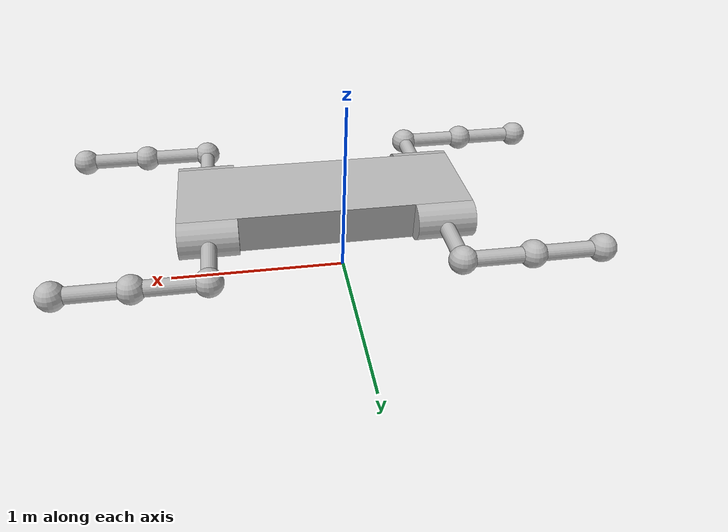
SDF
<?xml version='1.0'?>
<sdf version='1.6'>
  <model name='pigot'>
    <link name='body'>
      <pose frame=''>0 0 0 0 -0 0</pose>
      <inertial>
        <pose frame=''>0.000988 0.000494 0.003487 0 -0 0</pose>
        <mass>2.51756</mass>
        <inertia>
          <ixx>0.0145031</ixx>
          <ixy>-0.000174978</ixy>
          <ixz>-0.00123511</ixz>
          <iyy>0.110285</iyy>
          <iyz>-0.000617577</iyz>
          <izz>0.111214</izz>
        </inertia>
      </inertial>
      <self_collide>0</self_collide>
      <kinematic>0</kinematic>
      <visual name='body_fixed_joint_lump__lf_ball_2_visual'>
        <pose frame=''>0.14166 0.07083 0.5 0 -0 0</pose>
        <geometry>
          <box>
            <size>1.5 0.5 0.2</size>
          </box>
        </geometry>
        <cast_shadows>1</cast_shadows>
        <transparency>0</transparency>
      </visual>
      <visual name='body_fixed_joint_lump__lf_ball_2_visual_1'>
        <pose frame=''>0.74166 -0.17916 0.5 3.14159 1.57079 -3.14159</pose>
        <geometry>
          <cylinder>
            <length>0.3</length>
            <radius>0.1</radius>
          </cylinder>
        </geometry>
        <cast_shadows>1</cast_shadows>
        <transparency>0</transparency>
      </visual>
      <visual name='body_fixed_joint_lump__lf_ball_2_visual_2'>
        <pose frame=''>-0.45833 -0.17916 0.5 3.14159 1.57079 -3.14159</pose>
        <geometry>
          <cylinder>
            <length>0.3</length>
            <radius>0.1</radius>
          </cylinder>
        </geometry>
        <cast_shadows>1</cast_shadows>
        <transparency>0</transparency>
      </visual>
      <visual name='body_fixed_joint_lump__lf_ball_2_visual_3'>
        <pose frame=''>0.74166 0.32083 0.5 3.14159 1.57079 -3.14159</pose>
        <geometry>
          <cylinder>
            <length>0.3</length>
            <radius>0.1</radius>
          </cylinder>
        </geometry>
        <cast_shadows>1</cast_shadows>
        <transparency>0</transparency>
      </visual>
      <visual name='body_fixed_joint_lump__lf_ball_2_visual_4'>
        <pose frame=''>-0.45833 0.32083 0.5 3.14159 1.57079 -3.14159</pose>
        <geometry>
          <cylinder>
            <length>0.3</length>
            <radius>0.1</radius>
          </cylinder>
        </geometry>
        <cast_shadows>1</cast_shadows>
        <transparency>0</transparency>
      </visual>
      <collision name='body_fixed_joint_lump__pigot__collision_collision_1'>
        <laser_retro>0</laser_retro>
        <max_contacts>10</max_contacts>
        <pose frame=''>0.74166 -0.17916 0.5 3.14159 1.57079 -3.14159</pose>
        <geometry>
          <cylinder>
            <radius>0.1</radius>
            <length>0.3</length>
          </cylinder>
        </geometry>
        <surface>
          <friction>
            <ode>
              <mu>1</mu>
              <mu2>1</mu2>
              <fdir1>0 0 0</fdir1>
              <slip1>0</slip1>
              <slip2>0</slip2>
            </ode>
            <torsional>
              <coefficient>1</coefficient>
              <patch_radius>0</patch_radius>
              <surface_radius>0</surface_radius>
              <use_patch_radius>1</use_patch_radius>
              <ode>
                <slip>0</slip>
              </ode>
            </torsional>
          </friction>
          <bounce>
            <restitution_coefficient>0</restitution_coefficient>
            <threshold>1e+06</threshold>
          </bounce>
          <contact>
            <collide_without_contact>0</collide_without_contact>
            <collide_without_contact_bitmask>1</collide_without_contact_bitmask>
            <collide_bitmask>1</collide_bitmask>
            <ode>
              <soft_cfm>0</soft_cfm>
              <soft_erp>0.2</soft_erp>
              <kp>1e+13</kp>
              <kd>1</kd>
              <max_vel>0.01</max_vel>
              <min_depth>0</min_depth>
            </ode>
            <bullet>
              <split_impulse>1</split_impulse>
              <split_impulse_penetration_threshold>-0.01</split_impulse_penetration_threshold>
              <soft_cfm>0</soft_cfm>
              <soft_erp>0.2</soft_erp>
              <kp>1e+13</kp>
              <kd>1</kd>
            </bullet>
          </contact>
        </surface>
      </collision>
      <collision name='body_fixed_joint_lump__pigot__collision_collision'>
        <laser_retro>0</laser_retro>
        <max_contacts>10</max_contacts>
        <pose frame=''>0.14166 0.07083 0.5 0 -0 0</pose>
        <geometry>
          <box>
            <size>1.5 0.5 0.2</size>
          </box>
        </geometry>
        <surface>
          <friction>
            <ode>
              <mu>1</mu>
              <mu2>1</mu2>
              <fdir1>0 0 0</fdir1>
              <slip1>0</slip1>
              <slip2>0</slip2>
            </ode>
            <torsional>
              <coefficient>1</coefficient>
              <patch_radius>0</patch_radius>
              <surface_radius>0</surface_radius>
              <use_patch_radius>1</use_patch_radius>
              <ode>
                <slip>0</slip>
              </ode>
            </torsional>
          </friction>
          <bounce>
            <restitution_coefficient>0</restitution_coefficient>
            <threshold>1e+06</threshold>
          </bounce>
          <contact>
            <collide_without_contact>0</collide_without_contact>
            <collide_without_contact_bitmask>1</collide_without_contact_bitmask>
            <collide_bitmask>1</collide_bitmask>
            <ode>
              <soft_cfm>0</soft_cfm>
              <soft_erp>0.2</soft_erp>
              <kp>1e+13</kp>
              <kd>1</kd>
              <max_vel>0.01</max_vel>
              <min_depth>0</min_depth>
            </ode>
            <bullet>
              <split_impulse>1</split_impulse>
              <split_impulse_penetration_threshold>-0.01</split_impulse_penetration_threshold>
              <soft_cfm>0</soft_cfm>
              <soft_erp>0.2</soft_erp>
              <kp>1e+13</kp>
              <kd>1</kd>
            </bullet>
          </contact>
        </surface>
      </collision>
      <collision name='body_fixed_joint_lump__pigot__collision_collision_2'>
        <laser_retro>0</laser_retro>
        <max_contacts>10</max_contacts>
        <pose frame=''>-0.45833 -0.17916 0.5 3.14159 1.57079 -3.14159</pose>
        <geometry>
          <cylinder>
            <radius>0.1</radius>
            <length>0.3</length>
          </cylinder>
        </geometry>
        <surface>
          <friction>
            <ode>
              <mu>1</mu>
              <mu2>1</mu2>
              <fdir1>0 0 0</fdir1>
              <slip1>0</slip1>
              <slip2>0</slip2>
            </ode>
            <torsional>
              <coefficient>1</coefficient>
              <patch_radius>0</patch_radius>
              <surface_radius>0</surface_radius>
              <use_patch_radius>1</use_patch_radius>
              <ode>
                <slip>0</slip>
              </ode>
            </torsional>
          </friction>
          <bounce>
            <restitution_coefficient>0</restitution_coefficient>
            <threshold>1e+06</threshold>
          </bounce>
          <contact>
            <collide_without_contact>0</collide_without_contact>
            <collide_without_contact_bitmask>1</collide_without_contact_bitmask>
            <collide_bitmask>1</collide_bitmask>
            <ode>
              <soft_cfm>0</soft_cfm>
              <soft_erp>0.2</soft_erp>
              <kp>1e+13</kp>
              <kd>1</kd>
              <max_vel>0.01</max_vel>
              <min_depth>0</min_depth>
            </ode>
            <bullet>
              <split_impulse>1</split_impulse>
              <split_impulse_penetration_threshold>-0.01</split_impulse_penetration_threshold>
              <soft_cfm>0</soft_cfm>
              <soft_erp>0.2</soft_erp>
              <kp>1e+13</kp>
              <kd>1</kd>
            </bullet>
          </contact>
        </surface>
      </collision>
      <collision name='body_fixed_joint_lump__pigot__collision_collision_3'>
        <laser_retro>0</laser_retro>
        <max_contacts>10</max_contacts>
        <pose frame=''>0.74166 0.32083 0.5 3.14159 1.57079 -3.14159</pose>
        <geometry>
          <cylinder>
            <radius>0.1</radius>
            <length>0.3</length>
          </cylinder>
        </geometry>
        <surface>
          <friction>
            <ode>
              <mu>1</mu>
              <mu2>1</mu2>
              <fdir1>0 0 0</fdir1>
              <slip1>0</slip1>
              <slip2>0</slip2>
            </ode>
            <torsional>
              <coefficient>1</coefficient>
              <patch_radius>0</patch_radius>
              <surface_radius>0</surface_radius>
              <use_patch_radius>1</use_patch_radius>
              <ode>
                <slip>0</slip>
              </ode>
            </torsional>
          </friction>
          <bounce>
            <restitution_coefficient>0</restitution_coefficient>
            <threshold>1e+06</threshold>
          </bounce>
          <contact>
            <collide_without_contact>0</collide_without_contact>
            <collide_without_contact_bitmask>1</collide_without_contact_bitmask>
            <collide_bitmask>1</collide_bitmask>
            <ode>
              <soft_cfm>0</soft_cfm>
              <soft_erp>0.2</soft_erp>
              <kp>1e+13</kp>
              <kd>1</kd>
              <max_vel>0.01</max_vel>
              <min_depth>0</min_depth>
            </ode>
            <bullet>
              <split_impulse>1</split_impulse>
              <split_impulse_penetration_threshold>-0.01</split_impulse_penetration_threshold>
              <soft_cfm>0</soft_cfm>
              <soft_erp>0.2</soft_erp>
              <kp>1e+13</kp>
              <kd>1</kd>
            </bullet>
          </contact>
        </surface>
      </collision>
      <collision name='body_fixed_joint_lump__pigot__collision_collision_4'>
        <laser_retro>0</laser_retro>
        <max_contacts>10</max_contacts>
        <pose frame=''>-0.45833 0.32083 0.5 3.14159 1.57079 -3.14159</pose>
        <geometry>
          <cylinder>
            <radius>0.1</radius>
            <length>0.3</length>
          </cylinder>
        </geometry>
        <surface>
          <friction>
            <ode>
              <mu>1</mu>
              <mu2>1</mu2>
              <fdir1>0 0 0</fdir1>
              <slip1>0</slip1>
              <slip2>0</slip2>
            </ode>
            <torsional>
              <coefficient>1</coefficient>
              <patch_radius>0</patch_radius>
              <surface_radius>0</surface_radius>
              <use_patch_radius>1</use_patch_radius>
              <ode>
                <slip>0</slip>
              </ode>
            </torsional>
          </friction>
          <bounce>
            <restitution_coefficient>0</restitution_coefficient>
            <threshold>1e+06</threshold>
          </bounce>
          <contact>
            <collide_without_contact>0</collide_without_contact>
            <collide_without_contact_bitmask>1</collide_without_contact_bitmask>
            <collide_bitmask>1</collide_bitmask>
            <ode>
              <soft_cfm>0</soft_cfm>
              <soft_erp>0.2</soft_erp>
              <kp>1e+13</kp>
              <kd>1</kd>
              <max_vel>0.01</max_vel>
              <min_depth>0</min_depth>
            </ode>
            <bullet>
              <split_impulse>1</split_impulse>
              <split_impulse_penetration_threshold>-0.01</split_impulse_penetration_threshold>
              <soft_cfm>0</soft_cfm>
              <soft_erp>0.2</soft_erp>
              <kp>1e+13</kp>
              <kd>1</kd>
            </bullet>
          </contact>
        </surface>
      </collision>
    </link>
    <link name='lb_link_1'>
      <pose frame=''>0.74166 -0.17916 0.5 1.5708 -0 0</pose>
      <inertial>
        <pose frame=''>0 0 0.349153 0 -0 0</pose>
        <mass>1.0024</mass>
        <inertia>
          <ixx>0.100328</ixx>
          <ixy>0</ixy>
          <ixz>0</ixz>
          <iyy>0.100328</iyy>
          <iyz>0</iyz>
          <izz>0.100002</izz>
        </inertia>
      </inertial>
      <self_collide>0</self_collide>
      <kinematic>0</kinematic>
      <visual name='lb_link_1_fixed_joint_lump__lf_ball_2_visual'>
        <pose frame=''>0 0 0.175 0 -0 0</pose>
        <geometry>
          <cylinder>
            <length>0.35</length>
            <radius>0.04</radius>
          </cylinder>
        </geometry>
        <cast_shadows>1</cast_shadows>
        <transparency>0</transparency>
      </visual>
      <visual name='lb_link_1_fixed_joint_lump__lf_ball_2_visual_1'>
        <pose frame=''>0 0 0.34999 -1.57079 0 0</pose>
        <geometry>
          <sphere>
            <radius>0.07</radius>
          </sphere>
        </geometry>
        <cast_shadows>1</cast_shadows>
        <transparency>0</transparency>
      </visual>
      <collision name='lb_link_1_fixed_joint_lump__pigot__collision_collision'>
        <laser_retro>0</laser_retro>
        <max_contacts>10</max_contacts>
        <pose frame=''>0 0 0.175 0 -0 0</pose>
        <geometry>
          <cylinder>
            <radius>0.04</radius>
            <length>0.35</length>
          </cylinder>
        </geometry>
        <surface>
          <friction>
            <ode>
              <mu>1</mu>
              <mu2>1</mu2>
              <fdir1>0 0 0</fdir1>
              <slip1>0</slip1>
              <slip2>0</slip2>
            </ode>
            <torsional>
              <coefficient>1</coefficient>
              <patch_radius>0</patch_radius>
              <surface_radius>0</surface_radius>
              <use_patch_radius>1</use_patch_radius>
              <ode>
                <slip>0</slip>
              </ode>
            </torsional>
          </friction>
          <bounce>
            <restitution_coefficient>0</restitution_coefficient>
            <threshold>1e+06</threshold>
          </bounce>
          <contact>
            <collide_without_contact>0</collide_without_contact>
            <collide_without_contact_bitmask>1</collide_without_contact_bitmask>
            <collide_bitmask>1</collide_bitmask>
            <ode>
              <soft_cfm>0</soft_cfm>
              <soft_erp>0.2</soft_erp>
              <kp>1e+13</kp>
              <kd>1</kd>
              <max_vel>0.01</max_vel>
              <min_depth>0</min_depth>
            </ode>
            <bullet>
              <split_impulse>1</split_impulse>
              <split_impulse_penetration_threshold>-0.01</split_impulse_penetration_threshold>
              <soft_cfm>0</soft_cfm>
              <soft_erp>0.2</soft_erp>
              <kp>1e+13</kp>
              <kd>1</kd>
            </bullet>
          </contact>
        </surface>
      </collision>
      <collision name='lb_link_1_fixed_joint_lump__pigot__collision_collision_1'>
        <laser_retro>0</laser_retro>
        <max_contacts>10</max_contacts>
        <pose frame=''>0 0 0.34999 -1.57079 0 0</pose>
        <geometry>
          <sphere>
            <radius>0.07</radius>
          </sphere>
        </geometry>
        <surface>
          <friction>
            <ode>
              <mu>1</mu>
              <mu2>1</mu2>
              <fdir1>0 0 0</fdir1>
              <slip1>0</slip1>
              <slip2>0</slip2>
            </ode>
            <torsional>
              <coefficient>1</coefficient>
              <patch_radius>0</patch_radius>
              <surface_radius>0</surface_radius>
              <use_patch_radius>1</use_patch_radius>
              <ode>
                <slip>0</slip>
              </ode>
            </torsional>
          </friction>
          <bounce>
            <restitution_coefficient>0</restitution_coefficient>
            <threshold>1e+06</threshold>
          </bounce>
          <contact>
            <collide_without_contact>0</collide_without_contact>
            <collide_without_contact_bitmask>1</collide_without_contact_bitmask>
            <collide_bitmask>1</collide_bitmask>
            <ode>
              <soft_cfm>0</soft_cfm>
              <soft_erp>0.2</soft_erp>
              <kp>1e+13</kp>
              <kd>1</kd>
              <max_vel>0.01</max_vel>
              <min_depth>0</min_depth>
            </ode>
            <bullet>
              <split_impulse>1</split_impulse>
              <split_impulse_penetration_threshold>-0.01</split_impulse_penetration_threshold>
              <soft_cfm>0</soft_cfm>
              <soft_erp>0.2</soft_erp>
              <kp>1e+13</kp>
              <kd>1</kd>
            </bullet>
          </contact>
        </surface>
      </collision>
    </link>
    <link name='lb_link_2'>
      <pose frame=''>0.74166 -0.52915 0.5 1.5708 -1.1e-05 1.57078</pose>
      <inertial>
        <pose frame=''>0 0 0.349163 0 -0 0</pose>
        <mass>1.0024</mass>
        <inertia>
          <ixx>0.100328</ixx>
          <ixy>-1.05879e-22</ixy>
          <ixz>0</ixz>
          <iyy>0.100328</iyy>
          <iyz>0</iyz>
          <izz>0.100002</izz>
        </inertia>
      </inertial>
      <self_collide>0</self_collide>
      <kinematic>0</kinematic>
      <visual name='lb_link_2_fixed_joint_lump__lf_ball_2_visual'>
        <pose frame=''>0 0 0.175 0 -0 0</pose>
        <geometry>
          <cylinder>
            <length>0.35</length>
            <radius>0.04</radius>
          </cylinder>
        </geometry>
        <cast_shadows>1</cast_shadows>
        <transparency>0</transparency>
      </visual>
      <visual name='lb_link_2_fixed_joint_lump__lf_ball_2_visual_1'>
        <pose frame=''>0 0 0.35 3.1369 -1.57079 1.57549</pose>
        <geometry>
          <sphere>
            <radius>0.07</radius>
          </sphere>
        </geometry>
        <cast_shadows>1</cast_shadows>
        <transparency>0</transparency>
      </visual>
      <collision name='lb_link_2_fixed_joint_lump__pigot__collision_collision'>
        <laser_retro>0</laser_retro>
        <max_contacts>10</max_contacts>
        <pose frame=''>0 0 0.175 0 -0 0</pose>
        <geometry>
          <cylinder>
            <radius>0.04</radius>
            <length>0.35</length>
          </cylinder>
        </geometry>
        <surface>
          <friction>
            <ode>
              <mu>1</mu>
              <mu2>1</mu2>
              <fdir1>0 0 0</fdir1>
              <slip1>0</slip1>
              <slip2>0</slip2>
            </ode>
            <torsional>
              <coefficient>1</coefficient>
              <patch_radius>0</patch_radius>
              <surface_radius>0</surface_radius>
              <use_patch_radius>1</use_patch_radius>
              <ode>
                <slip>0</slip>
              </ode>
            </torsional>
          </friction>
          <bounce>
            <restitution_coefficient>0</restitution_coefficient>
            <threshold>1e+06</threshold>
          </bounce>
          <contact>
            <collide_without_contact>0</collide_without_contact>
            <collide_without_contact_bitmask>1</collide_without_contact_bitmask>
            <collide_bitmask>1</collide_bitmask>
            <ode>
              <soft_cfm>0</soft_cfm>
              <soft_erp>0.2</soft_erp>
              <kp>1e+13</kp>
              <kd>1</kd>
              <max_vel>0.01</max_vel>
              <min_depth>0</min_depth>
            </ode>
            <bullet>
              <split_impulse>1</split_impulse>
              <split_impulse_penetration_threshold>-0.01</split_impulse_penetration_threshold>
              <soft_cfm>0</soft_cfm>
              <soft_erp>0.2</soft_erp>
              <kp>1e+13</kp>
              <kd>1</kd>
            </bullet>
          </contact>
        </surface>
      </collision>
      <collision name='lb_link_2_fixed_joint_lump__pigot__collision_collision_1'>
        <laser_retro>0</laser_retro>
        <max_contacts>10</max_contacts>
        <pose frame=''>0 0 0.35 3.14159 -1.57079 1.5708</pose>
        <geometry>
          <sphere>
            <radius>0.07</radius>
          </sphere>
        </geometry>
        <surface>
          <friction>
            <ode>
              <mu>1</mu>
              <mu2>1</mu2>
              <fdir1>0 0 0</fdir1>
              <slip1>0</slip1>
              <slip2>0</slip2>
            </ode>
            <torsional>
              <coefficient>1</coefficient>
              <patch_radius>0</patch_radius>
              <surface_radius>0</surface_radius>
              <use_patch_radius>1</use_patch_radius>
              <ode>
                <slip>0</slip>
              </ode>
            </torsional>
          </friction>
          <bounce>
            <restitution_coefficient>0</restitution_coefficient>
            <threshold>1e+06</threshold>
          </bounce>
          <contact>
            <collide_without_contact>0</collide_without_contact>
            <collide_without_contact_bitmask>1</collide_without_contact_bitmask>
            <collide_bitmask>1</collide_bitmask>
            <ode>
              <soft_cfm>0</soft_cfm>
              <soft_erp>0.2</soft_erp>
              <kp>1e+13</kp>
              <kd>1</kd>
              <max_vel>0.01</max_vel>
              <min_depth>0</min_depth>
            </ode>
            <bullet>
              <split_impulse>1</split_impulse>
              <split_impulse_penetration_threshold>-0.01</split_impulse_penetration_threshold>
              <soft_cfm>0</soft_cfm>
              <soft_erp>0.2</soft_erp>
              <kp>1e+13</kp>
              <kd>1</kd>
            </bullet>
          </contact>
        </surface>
      </collision>
    </link>
    <link name='lb_link_3'>
      <pose frame=''>1.09166 -0.529154 0.5 1.5708 -1.1e-05 1.57078</pose>
      <inertial>
        <pose frame=''>0 0 0.349163 0 -0 0</pose>
        <mass>1.0024</mass>
        <inertia>
          <ixx>0.100328</ixx>
          <ixy>-1.05879e-22</ixy>
          <ixz>0</ixz>
          <iyy>0.100328</iyy>
          <iyz>0</iyz>
          <izz>0.100002</izz>
        </inertia>
      </inertial>
      <self_collide>0</self_collide>
      <kinematic>0</kinematic>
      <visual name='lb_link_3_fixed_joint_lump__lf_ball_2_visual'>
        <pose frame=''>0 0 0.175 0 -0 0</pose>
        <geometry>
          <cylinder>
            <length>0.35</length>
            <radius>0.04</radius>
          </cylinder>
        </geometry>
        <cast_shadows>1</cast_shadows>
        <transparency>0</transparency>
      </visual>
      <visual name='lb_link_3_fixed_joint_lump__lf_ball_2_visual_1'>
        <pose frame=''>0 0 0.35 3.1369 -1.57079 1.57549</pose>
        <geometry>
          <sphere>
            <radius>0.07</radius>
          </sphere>
        </geometry>
        <cast_shadows>1</cast_shadows>
        <transparency>0</transparency>
      </visual>
      <collision name='lb_link_3_fixed_joint_lump__pigot__collision_collision'>
        <laser_retro>0</laser_retro>
        <max_contacts>10</max_contacts>
        <pose frame=''>0 0 0.175 0 -0 0</pose>
        <geometry>
          <cylinder>
            <radius>0.04</radius>
            <length>0.35</length>
          </cylinder>
        </geometry>
        <surface>
          <friction>
            <ode>
              <mu>1</mu>
              <mu2>1</mu2>
              <fdir1>0 0 0</fdir1>
              <slip1>0</slip1>
              <slip2>0</slip2>
            </ode>
            <torsional>
              <coefficient>1</coefficient>
              <patch_radius>0</patch_radius>
              <surface_radius>0</surface_radius>
              <use_patch_radius>1</use_patch_radius>
              <ode>
                <slip>0</slip>
              </ode>
            </torsional>
          </friction>
          <bounce>
            <restitution_coefficient>0</restitution_coefficient>
            <threshold>1e+06</threshold>
          </bounce>
          <contact>
            <collide_without_contact>0</collide_without_contact>
            <collide_without_contact_bitmask>1</collide_without_contact_bitmask>
            <collide_bitmask>1</collide_bitmask>
            <ode>
              <soft_cfm>0</soft_cfm>
              <soft_erp>0.2</soft_erp>
              <kp>1e+13</kp>
              <kd>1</kd>
              <max_vel>0.01</max_vel>
              <min_depth>0</min_depth>
            </ode>
            <bullet>
              <split_impulse>1</split_impulse>
              <split_impulse_penetration_threshold>-0.01</split_impulse_penetration_threshold>
              <soft_cfm>0</soft_cfm>
              <soft_erp>0.2</soft_erp>
              <kp>1e+13</kp>
              <kd>1</kd>
            </bullet>
          </contact>
        </surface>
      </collision>
      <collision name='lb_link_3_fixed_joint_lump__pigot__collision_collision_1'>
        <laser_retro>0</laser_retro>
        <max_contacts>10</max_contacts>
        <pose frame=''>0 0 0.35 3.14159 -1.57079 1.5708</pose>
        <geometry>
          <sphere>
            <radius>0.07</radius>
          </sphere>
        </geometry>
        <surface>
          <friction>
            <ode>
              <mu>1</mu>
              <mu2>1</mu2>
              <fdir1>0 0 0</fdir1>
              <slip1>0</slip1>
              <slip2>0</slip2>
            </ode>
            <torsional>
              <coefficient>1</coefficient>
              <patch_radius>0</patch_radius>
              <surface_radius>0</surface_radius>
              <use_patch_radius>1</use_patch_radius>
              <ode>
                <slip>0</slip>
              </ode>
            </torsional>
          </friction>
          <bounce>
            <restitution_coefficient>0</restitution_coefficient>
            <threshold>1e+06</threshold>
          </bounce>
          <contact>
            <collide_without_contact>0</collide_without_contact>
            <collide_without_contact_bitmask>1</collide_without_contact_bitmask>
            <collide_bitmask>1</collide_bitmask>
            <ode>
              <soft_cfm>0</soft_cfm>
              <soft_erp>0.2</soft_erp>
              <kp>1e+13</kp>
              <kd>1</kd>
              <max_vel>0.01</max_vel>
              <min_depth>0</min_depth>
            </ode>
            <bullet>
              <split_impulse>1</split_impulse>
              <split_impulse_penetration_threshold>-0.01</split_impulse_penetration_threshold>
              <soft_cfm>0</soft_cfm>
              <soft_erp>0.2</soft_erp>
              <kp>1e+13</kp>
              <kd>1</kd>
            </bullet>
          </contact>
        </surface>
      </collision>
    </link>
    <link name='lf_link_1'>
      <pose frame=''>-0.45833 -0.17916 0.5 1.5708 -0 0</pose>
      <inertial>
        <pose frame=''>0 0 0.349153 0 -0 0</pose>
        <mass>1.0024</mass>
        <inertia>
          <ixx>0.100328</ixx>
          <ixy>0</ixy>
          <ixz>0</ixz>
          <iyy>0.100328</iyy>
          <iyz>0</iyz>
          <izz>0.100002</izz>
        </inertia>
      </inertial>
      <self_collide>0</self_collide>
      <kinematic>0</kinematic>
      <visual name='lf_link_1_fixed_joint_lump__lf_ball_2_visual'>
        <pose frame=''>0 0 0.175 0 -0 0</pose>
        <geometry>
          <cylinder>
            <length>0.35</length>
            <radius>0.04</radius>
          </cylinder>
        </geometry>
        <cast_shadows>1</cast_shadows>
        <transparency>0</transparency>
      </visual>
      <visual name='lf_link_1_fixed_joint_lump__lf_ball_1_visual_1'>
        <pose frame=''>0 0 0.34999 -1.57079 0 0</pose>
        <geometry>
          <sphere>
            <radius>0.07</radius>
          </sphere>
        </geometry>
        <cast_shadows>1</cast_shadows>
        <transparency>0</transparency>
      </visual>
      <collision name='lf_link_1_fixed_joint_lump__pigot__collision_collision'>
        <laser_retro>0</laser_retro>
        <max_contacts>10</max_contacts>
        <pose frame=''>0 0 0.175 0 -0 0</pose>
        <geometry>
          <cylinder>
            <radius>0.04</radius>
            <length>0.35</length>
          </cylinder>
        </geometry>
        <surface>
          <friction>
            <ode>
              <mu>1</mu>
              <mu2>1</mu2>
              <fdir1>0 0 0</fdir1>
              <slip1>0</slip1>
              <slip2>0</slip2>
            </ode>
            <torsional>
              <coefficient>1</coefficient>
              <patch_radius>0</patch_radius>
              <surface_radius>0</surface_radius>
              <use_patch_radius>1</use_patch_radius>
              <ode>
                <slip>0</slip>
              </ode>
            </torsional>
          </friction>
          <bounce>
            <restitution_coefficient>0</restitution_coefficient>
            <threshold>1e+06</threshold>
          </bounce>
          <contact>
            <collide_without_contact>0</collide_without_contact>
            <collide_without_contact_bitmask>1</collide_without_contact_bitmask>
            <collide_bitmask>1</collide_bitmask>
            <ode>
              <soft_cfm>0</soft_cfm>
              <soft_erp>0.2</soft_erp>
              <kp>1e+13</kp>
              <kd>1</kd>
              <max_vel>0.01</max_vel>
              <min_depth>0</min_depth>
            </ode>
            <bullet>
              <split_impulse>1</split_impulse>
              <split_impulse_penetration_threshold>-0.01</split_impulse_penetration_threshold>
              <soft_cfm>0</soft_cfm>
              <soft_erp>0.2</soft_erp>
              <kp>1e+13</kp>
              <kd>1</kd>
            </bullet>
          </contact>
        </surface>
      </collision>
      <collision name='lf_link_1_fixed_joint_lump__pigot__collision_collision_1'>
        <laser_retro>0</laser_retro>
        <max_contacts>10</max_contacts>
        <pose frame=''>0 0 0.34999 -1.57079 0 0</pose>
        <geometry>
          <sphere>
            <radius>0.07</radius>
          </sphere>
        </geometry>
        <surface>
          <friction>
            <ode>
              <mu>1</mu>
              <mu2>1</mu2>
              <fdir1>0 0 0</fdir1>
              <slip1>0</slip1>
              <slip2>0</slip2>
            </ode>
            <torsional>
              <coefficient>1</coefficient>
              <patch_radius>0</patch_radius>
              <surface_radius>0</surface_radius>
              <use_patch_radius>1</use_patch_radius>
              <ode>
                <slip>0</slip>
              </ode>
            </torsional>
          </friction>
          <bounce>
            <restitution_coefficient>0</restitution_coefficient>
            <threshold>1e+06</threshold>
          </bounce>
          <contact>
            <collide_without_contact>0</collide_without_contact>
            <collide_without_contact_bitmask>1</collide_without_contact_bitmask>
            <collide_bitmask>1</collide_bitmask>
            <ode>
              <soft_cfm>0</soft_cfm>
              <soft_erp>0.2</soft_erp>
              <kp>1e+13</kp>
              <kd>1</kd>
              <max_vel>0.01</max_vel>
              <min_depth>0</min_depth>
            </ode>
            <bullet>
              <split_impulse>1</split_impulse>
              <split_impulse_penetration_threshold>-0.01</split_impulse_penetration_threshold>
              <soft_cfm>0</soft_cfm>
              <soft_erp>0.2</soft_erp>
              <kp>1e+13</kp>
              <kd>1</kd>
            </bullet>
          </contact>
        </surface>
      </collision>
    </link>
    <link name='lf_link_2'>
      <pose frame=''>-0.45833 -0.52916 0.5 1.5708 -1.1e-05 1.57078</pose>
      <inertial>
        <pose frame=''>0 0 -0.349153 0 -0 0</pose>
        <mass>1.0024</mass>
        <inertia>
          <ixx>0.100328</ixx>
          <ixy>-1.05879e-22</ixy>
          <ixz>0</ixz>
          <iyy>0.100328</iyy>
          <iyz>0</iyz>
          <izz>0.100002</izz>
        </inertia>
      </inertial>
      <self_collide>0</self_collide>
      <kinematic>0</kinematic>
      <visual name='lf_link_2_fixed_joint_lump__lf_ball_2_visual'>
        <pose frame=''>0 0 -0.175 0 -0 0</pose>
        <geometry>
          <cylinder>
            <length>0.35</length>
            <radius>0.04</radius>
          </cylinder>
        </geometry>
        <cast_shadows>1</cast_shadows>
        <transparency>0</transparency>
      </visual>
      <visual name='lf_link_2_fixed_joint_lump__lf_ball_2_visual_1'>
        <pose frame=''>0 0 -0.34999 3.1369 -1.57079 1.57549</pose>
        <geometry>
          <sphere>
            <radius>0.07</radius>
          </sphere>
        </geometry>
        <cast_shadows>1</cast_shadows>
        <transparency>0</transparency>
      </visual>
      <collision name='lf_link_2_fixed_joint_lump__pigot__collision_collision'>
        <laser_retro>0</laser_retro>
        <max_contacts>10</max_contacts>
        <pose frame=''>0 0 -0.175 0 -0 0</pose>
        <geometry>
          <cylinder>
            <radius>0.04</radius>
            <length>0.35</length>
          </cylinder>
        </geometry>
        <surface>
          <friction>
            <ode>
              <mu>1</mu>
              <mu2>1</mu2>
              <fdir1>0 0 0</fdir1>
              <slip1>0</slip1>
              <slip2>0</slip2>
            </ode>
            <torsional>
              <coefficient>1</coefficient>
              <patch_radius>0</patch_radius>
              <surface_radius>0</surface_radius>
              <use_patch_radius>1</use_patch_radius>
              <ode>
                <slip>0</slip>
              </ode>
            </torsional>
          </friction>
          <bounce>
            <restitution_coefficient>0</restitution_coefficient>
            <threshold>1e+06</threshold>
          </bounce>
          <contact>
            <collide_without_contact>0</collide_without_contact>
            <collide_without_contact_bitmask>1</collide_without_contact_bitmask>
            <collide_bitmask>1</collide_bitmask>
            <ode>
              <soft_cfm>0</soft_cfm>
              <soft_erp>0.2</soft_erp>
              <kp>1e+13</kp>
              <kd>1</kd>
              <max_vel>0.01</max_vel>
              <min_depth>0</min_depth>
            </ode>
            <bullet>
              <split_impulse>1</split_impulse>
              <split_impulse_penetration_threshold>-0.01</split_impulse_penetration_threshold>
              <soft_cfm>0</soft_cfm>
              <soft_erp>0.2</soft_erp>
              <kp>1e+13</kp>
              <kd>1</kd>
            </bullet>
          </contact>
        </surface>
      </collision>
      <collision name='lf_link_2_fixed_joint_lump__pigot__collision_collision_1'>
        <laser_retro>0</laser_retro>
        <max_contacts>10</max_contacts>
        <pose frame=''>0 0 -0.34999 3.14159 -1.57079 1.5708</pose>
        <geometry>
          <sphere>
            <radius>0.07</radius>
          </sphere>
        </geometry>
        <surface>
          <friction>
            <ode>
              <mu>1</mu>
              <mu2>1</mu2>
              <fdir1>0 0 0</fdir1>
              <slip1>0</slip1>
              <slip2>0</slip2>
            </ode>
            <torsional>
              <coefficient>1</coefficient>
              <patch_radius>0</patch_radius>
              <surface_radius>0</surface_radius>
              <use_patch_radius>1</use_patch_radius>
              <ode>
                <slip>0</slip>
              </ode>
            </torsional>
          </friction>
          <bounce>
            <restitution_coefficient>0</restitution_coefficient>
            <threshold>1e+06</threshold>
          </bounce>
          <contact>
            <collide_without_contact>0</collide_without_contact>
            <collide_without_contact_bitmask>1</collide_without_contact_bitmask>
            <collide_bitmask>1</collide_bitmask>
            <ode>
              <soft_cfm>0</soft_cfm>
              <soft_erp>0.2</soft_erp>
              <kp>1e+13</kp>
              <kd>1</kd>
              <max_vel>0.01</max_vel>
              <min_depth>0</min_depth>
            </ode>
            <bullet>
              <split_impulse>1</split_impulse>
              <split_impulse_penetration_threshold>-0.01</split_impulse_penetration_threshold>
              <soft_cfm>0</soft_cfm>
              <soft_erp>0.2</soft_erp>
              <kp>1e+13</kp>
              <kd>1</kd>
            </bullet>
          </contact>
        </surface>
      </collision>
    </link>
    <link name='lf_link_3'>
      <pose frame=''>-0.80833 -0.529156 0.5 1.5708 -1.1e-05 1.57078</pose>
      <inertial>
        <pose frame=''>0 0 -0.349153 0 -0 0</pose>
        <mass>1.0024</mass>
        <inertia>
          <ixx>0.100328</ixx>
          <ixy>-1.05879e-22</ixy>
          <ixz>0</ixz>
          <iyy>0.100328</iyy>
          <iyz>0</iyz>
          <izz>0.100002</izz>
        </inertia>
      </inertial>
      <self_collide>0</self_collide>
      <kinematic>0</kinematic>
      <visual name='lf_link_3_fixed_joint_lump__lf_ball_2_visual'>
        <pose frame=''>0 0 -0.175 0 -0 0</pose>
        <geometry>
          <cylinder>
            <length>0.35</length>
            <radius>0.04</radius>
          </cylinder>
        </geometry>
        <cast_shadows>1</cast_shadows>
        <transparency>0</transparency>
      </visual>
      <visual name='lf_link_3_fixed_joint_lump__lf_ball_2_visual_1'>
        <pose frame=''>0 0 -0.34999 3.1369 -1.57079 1.57549</pose>
        <geometry>
          <sphere>
            <radius>0.07</radius>
          </sphere>
        </geometry>
        <cast_shadows>1</cast_shadows>
        <transparency>0</transparency>
      </visual>
      <collision name='lf_link_3_fixed_joint_lump__pigot__collision_collision'>
        <laser_retro>0</laser_retro>
        <max_contacts>10</max_contacts>
        <pose frame=''>0 0 -0.175 0 -0 0</pose>
        <geometry>
          <cylinder>
            <radius>0.04</radius>
            <length>0.35</length>
          </cylinder>
        </geometry>
        <surface>
          <friction>
            <ode>
              <mu>1</mu>
              <mu2>1</mu2>
              <fdir1>0 0 0</fdir1>
              <slip1>0</slip1>
              <slip2>0</slip2>
            </ode>
            <torsional>
              <coefficient>1</coefficient>
              <patch_radius>0</patch_radius>
              <surface_radius>0</surface_radius>
              <use_patch_radius>1</use_patch_radius>
              <ode>
                <slip>0</slip>
              </ode>
            </torsional>
          </friction>
          <bounce>
            <restitution_coefficient>0</restitution_coefficient>
            <threshold>1e+06</threshold>
          </bounce>
          <contact>
            <collide_without_contact>0</collide_without_contact>
            <collide_without_contact_bitmask>1</collide_without_contact_bitmask>
            <collide_bitmask>1</collide_bitmask>
            <ode>
              <soft_cfm>0</soft_cfm>
              <soft_erp>0.2</soft_erp>
              <kp>1e+13</kp>
              <kd>1</kd>
              <max_vel>0.01</max_vel>
              <min_depth>0</min_depth>
            </ode>
            <bullet>
              <split_impulse>1</split_impulse>
              <split_impulse_penetration_threshold>-0.01</split_impulse_penetration_threshold>
              <soft_cfm>0</soft_cfm>
              <soft_erp>0.2</soft_erp>
              <kp>1e+13</kp>
              <kd>1</kd>
            </bullet>
          </contact>
        </surface>
      </collision>
      <collision name='lf_link_3_fixed_joint_lump__pigot__collision_collision_1'>
        <laser_retro>0</laser_retro>
        <max_contacts>10</max_contacts>
        <pose frame=''>0 0 -0.34999 3.14159 -1.57079 1.5708</pose>
        <geometry>
          <sphere>
            <radius>0.07</radius>
          </sphere>
        </geometry>
        <surface>
          <friction>
            <ode>
              <mu>1</mu>
              <mu2>1</mu2>
              <fdir1>0 0 0</fdir1>
              <slip1>0</slip1>
              <slip2>0</slip2>
            </ode>
            <torsional>
              <coefficient>1</coefficient>
              <patch_radius>0</patch_radius>
              <surface_radius>0</surface_radius>
              <use_patch_radius>1</use_patch_radius>
              <ode>
                <slip>0</slip>
              </ode>
            </torsional>
          </friction>
          <bounce>
            <restitution_coefficient>0</restitution_coefficient>
            <threshold>1e+06</threshold>
          </bounce>
          <contact>
            <collide_without_contact>0</collide_without_contact>
            <collide_without_contact_bitmask>1</collide_without_contact_bitmask>
            <collide_bitmask>1</collide_bitmask>
            <ode>
              <soft_cfm>0</soft_cfm>
              <soft_erp>0.2</soft_erp>
              <kp>1e+13</kp>
              <kd>1</kd>
              <max_vel>0.01</max_vel>
              <min_depth>0</min_depth>
            </ode>
            <bullet>
              <split_impulse>1</split_impulse>
              <split_impulse_penetration_threshold>-0.01</split_impulse_penetration_threshold>
              <soft_cfm>0</soft_cfm>
              <soft_erp>0.2</soft_erp>
              <kp>1e+13</kp>
              <kd>1</kd>
            </bullet>
          </contact>
        </surface>
      </collision>
    </link>
    <link name='rb_link_1'>
      <pose frame=''>0.74166 0.32083 0.5 -1.57079 0 0</pose>
      <inertial>
        <pose frame=''>0 0 0.349163 0 -0 0</pose>
        <mass>1.0024</mass>
        <inertia>
          <ixx>0.100328</ixx>
          <ixy>0</ixy>
          <ixz>0</ixz>
          <iyy>0.100328</iyy>
          <iyz>0</iyz>
          <izz>0.100002</izz>
        </inertia>
      </inertial>
      <self_collide>0</self_collide>
      <kinematic>0</kinematic>
      <visual name='rb_link_1_fixed_joint_lump__lf_ball_2_visual'>
        <pose frame=''>0 0 0.175 0 -0 0</pose>
        <geometry>
          <cylinder>
            <length>0.35</length>
            <radius>0.04</radius>
          </cylinder>
        </geometry>
        <cast_shadows>1</cast_shadows>
        <transparency>0</transparency>
      </visual>
      <visual name='rb_link_1_fixed_joint_lump__lf_ball_2_visual_1'>
        <pose frame=''>0 0 0.35 1.57079 -0 0</pose>
        <geometry>
          <sphere>
            <radius>0.07</radius>
          </sphere>
        </geometry>
        <cast_shadows>1</cast_shadows>
        <transparency>0</transparency>
      </visual>
      <collision name='rb_link_1_fixed_joint_lump__pigot__collision_collision'>
        <laser_retro>0</laser_retro>
        <max_contacts>10</max_contacts>
        <pose frame=''>0 0 0.175 0 -0 0</pose>
        <geometry>
          <cylinder>
            <radius>0.04</radius>
            <length>0.35</length>
          </cylinder>
        </geometry>
        <surface>
          <friction>
            <ode>
              <mu>1</mu>
              <mu2>1</mu2>
              <fdir1>0 0 0</fdir1>
              <slip1>0</slip1>
              <slip2>0</slip2>
            </ode>
            <torsional>
              <coefficient>1</coefficient>
              <patch_radius>0</patch_radius>
              <surface_radius>0</surface_radius>
              <use_patch_radius>1</use_patch_radius>
              <ode>
                <slip>0</slip>
              </ode>
            </torsional>
          </friction>
          <bounce>
            <restitution_coefficient>0</restitution_coefficient>
            <threshold>1e+06</threshold>
          </bounce>
          <contact>
            <collide_without_contact>0</collide_without_contact>
            <collide_without_contact_bitmask>1</collide_without_contact_bitmask>
            <collide_bitmask>1</collide_bitmask>
            <ode>
              <soft_cfm>0</soft_cfm>
              <soft_erp>0.2</soft_erp>
              <kp>1e+13</kp>
              <kd>1</kd>
              <max_vel>0.01</max_vel>
              <min_depth>0</min_depth>
            </ode>
            <bullet>
              <split_impulse>1</split_impulse>
              <split_impulse_penetration_threshold>-0.01</split_impulse_penetration_threshold>
              <soft_cfm>0</soft_cfm>
              <soft_erp>0.2</soft_erp>
              <kp>1e+13</kp>
              <kd>1</kd>
            </bullet>
          </contact>
        </surface>
      </collision>
      <collision name='rb_link_1_fixed_joint_lump__pigot__collision_collision_1'>
        <laser_retro>0</laser_retro>
        <max_contacts>10</max_contacts>
        <pose frame=''>0 0 0.35 1.57079 -0 0</pose>
        <geometry>
          <sphere>
            <radius>0.07</radius>
          </sphere>
        </geometry>
        <surface>
          <friction>
            <ode>
              <mu>1</mu>
              <mu2>1</mu2>
              <fdir1>0 0 0</fdir1>
              <slip1>0</slip1>
              <slip2>0</slip2>
            </ode>
            <torsional>
              <coefficient>1</coefficient>
              <patch_radius>0</patch_radius>
              <surface_radius>0</surface_radius>
              <use_patch_radius>1</use_patch_radius>
              <ode>
                <slip>0</slip>
              </ode>
            </torsional>
          </friction>
          <bounce>
            <restitution_coefficient>0</restitution_coefficient>
            <threshold>1e+06</threshold>
          </bounce>
          <contact>
            <collide_without_contact>0</collide_without_contact>
            <collide_without_contact_bitmask>1</collide_without_contact_bitmask>
            <collide_bitmask>1</collide_bitmask>
            <ode>
              <soft_cfm>0</soft_cfm>
              <soft_erp>0.2</soft_erp>
              <kp>1e+13</kp>
              <kd>1</kd>
              <max_vel>0.01</max_vel>
              <min_depth>0</min_depth>
            </ode>
            <bullet>
              <split_impulse>1</split_impulse>
              <split_impulse_penetration_threshold>-0.01</split_impulse_penetration_threshold>
              <soft_cfm>0</soft_cfm>
              <soft_erp>0.2</soft_erp>
              <kp>1e+13</kp>
              <kd>1</kd>
            </bullet>
          </contact>
        </surface>
      </collision>
    </link>
    <link name='rb_link_2'>
      <pose frame=''>0.74166 0.67083 0.500002 1.57077 5e-06 1.57078</pose>
      <inertial>
        <pose frame=''>0 0 0.349163 0 -0 0</pose>
        <mass>1.0024</mass>
        <inertia>
          <ixx>0.100328</ixx>
          <ixy>-1.05879e-22</ixy>
          <ixz>0</ixz>
          <iyy>0.100328</iyy>
          <iyz>0</iyz>
          <izz>0.100002</izz>
        </inertia>
      </inertial>
      <self_collide>0</self_collide>
      <kinematic>0</kinematic>
      <visual name='rb_link_2_fixed_joint_lump__lf_ball_2_visual'>
        <pose frame=''>0 0 0.175 0 -0 0</pose>
        <geometry>
          <cylinder>
            <length>0.35</length>
            <radius>0.04</radius>
          </cylinder>
        </geometry>
        <cast_shadows>1</cast_shadows>
        <transparency>0</transparency>
      </visual>
      <visual name='rb_link_2_fixed_joint_lump__lf_ball_2_visual_1'>
        <pose frame=''>0 0 0.35 3.1369 -1.57079 1.57549</pose>
        <geometry>
          <sphere>
            <radius>0.07</radius>
          </sphere>
        </geometry>
        <cast_shadows>1</cast_shadows>
        <transparency>0</transparency>
      </visual>
      <collision name='rb_link_2_fixed_joint_lump__pigot__collision_collision'>
        <laser_retro>0</laser_retro>
        <max_contacts>10</max_contacts>
        <pose frame=''>0 0 0.175 0 -0 0</pose>
        <geometry>
          <cylinder>
            <radius>0.04</radius>
            <length>0.35</length>
          </cylinder>
        </geometry>
        <surface>
          <friction>
            <ode>
              <mu>1</mu>
              <mu2>1</mu2>
              <fdir1>0 0 0</fdir1>
              <slip1>0</slip1>
              <slip2>0</slip2>
            </ode>
            <torsional>
              <coefficient>1</coefficient>
              <patch_radius>0</patch_radius>
              <surface_radius>0</surface_radius>
              <use_patch_radius>1</use_patch_radius>
              <ode>
                <slip>0</slip>
              </ode>
            </torsional>
          </friction>
          <bounce>
            <restitution_coefficient>0</restitution_coefficient>
            <threshold>1e+06</threshold>
          </bounce>
          <contact>
            <collide_without_contact>0</collide_without_contact>
            <collide_without_contact_bitmask>1</collide_without_contact_bitmask>
            <collide_bitmask>1</collide_bitmask>
            <ode>
              <soft_cfm>0</soft_cfm>
              <soft_erp>0.2</soft_erp>
              <kp>1e+13</kp>
              <kd>1</kd>
              <max_vel>0.01</max_vel>
              <min_depth>0</min_depth>
            </ode>
            <bullet>
              <split_impulse>1</split_impulse>
              <split_impulse_penetration_threshold>-0.01</split_impulse_penetration_threshold>
              <soft_cfm>0</soft_cfm>
              <soft_erp>0.2</soft_erp>
              <kp>1e+13</kp>
              <kd>1</kd>
            </bullet>
          </contact>
        </surface>
      </collision>
      <collision name='rb_link_2_fixed_joint_lump__pigot__collision_collision_1'>
        <laser_retro>0</laser_retro>
        <max_contacts>10</max_contacts>
        <pose frame=''>0 0 0.35 3.14159 -1.57079 1.5708</pose>
        <geometry>
          <sphere>
            <radius>0.07</radius>
          </sphere>
        </geometry>
        <surface>
          <friction>
            <ode>
              <mu>1</mu>
              <mu2>1</mu2>
              <fdir1>0 0 0</fdir1>
              <slip1>0</slip1>
              <slip2>0</slip2>
            </ode>
            <torsional>
              <coefficient>1</coefficient>
              <patch_radius>0</patch_radius>
              <surface_radius>0</surface_radius>
              <use_patch_radius>1</use_patch_radius>
              <ode>
                <slip>0</slip>
              </ode>
            </torsional>
          </friction>
          <bounce>
            <restitution_coefficient>0</restitution_coefficient>
            <threshold>1e+06</threshold>
          </bounce>
          <contact>
            <collide_without_contact>0</collide_without_contact>
            <collide_without_contact_bitmask>1</collide_without_contact_bitmask>
            <collide_bitmask>1</collide_bitmask>
            <ode>
              <soft_cfm>0</soft_cfm>
              <soft_erp>0.2</soft_erp>
              <kp>1e+13</kp>
              <kd>1</kd>
              <max_vel>0.01</max_vel>
              <min_depth>0</min_depth>
            </ode>
            <bullet>
              <split_impulse>1</split_impulse>
              <split_impulse_penetration_threshold>-0.01</split_impulse_penetration_threshold>
              <soft_cfm>0</soft_cfm>
              <soft_erp>0.2</soft_erp>
              <kp>1e+13</kp>
              <kd>1</kd>
            </bullet>
          </contact>
        </surface>
      </collision>
    </link>
    <link name='rb_link_3'>
      <pose frame=''>1.09166 0.670826 0.50001 1.57077 5e-06 1.57078</pose>
      <inertial>
        <pose frame=''>0 0 0.349163 0 -0 0</pose>
        <mass>1.0024</mass>
        <inertia>
          <ixx>0.100328</ixx>
          <ixy>-1.05879e-22</ixy>
          <ixz>0</ixz>
          <iyy>0.100328</iyy>
          <iyz>0</iyz>
          <izz>0.100002</izz>
        </inertia>
      </inertial>
      <self_collide>0</self_collide>
      <kinematic>0</kinematic>
      <visual name='rb_link_3_fixed_joint_lump__lf_ball_2_visual'>
        <pose frame=''>0 0 0.175 0 -0 0</pose>
        <geometry>
          <cylinder>
            <length>0.35</length>
            <radius>0.04</radius>
          </cylinder>
        </geometry>
        <cast_shadows>1</cast_shadows>
        <transparency>0</transparency>
      </visual>
      <visual name='rb_link_3_fixed_joint_lump__lf_ball_2_visual_1'>
        <pose frame=''>0 0 0.35 3.1369 -1.57079 1.57549</pose>
        <geometry>
          <sphere>
            <radius>0.07</radius>
          </sphere>
        </geometry>
        <cast_shadows>1</cast_shadows>
        <transparency>0</transparency>
      </visual>
      <collision name='rb_link_3_fixed_joint_lump__pigot__collision_collision'>
        <laser_retro>0</laser_retro>
        <max_contacts>10</max_contacts>
        <pose frame=''>0 0 0.175 0 -0 0</pose>
        <geometry>
          <cylinder>
            <radius>0.04</radius>
            <length>0.35</length>
          </cylinder>
        </geometry>
        <surface>
          <friction>
            <ode>
              <mu>1</mu>
              <mu2>1</mu2>
              <fdir1>0 0 0</fdir1>
              <slip1>0</slip1>
              <slip2>0</slip2>
            </ode>
            <torsional>
              <coefficient>1</coefficient>
              <patch_radius>0</patch_radius>
              <surface_radius>0</surface_radius>
              <use_patch_radius>1</use_patch_radius>
              <ode>
                <slip>0</slip>
              </ode>
            </torsional>
          </friction>
          <bounce>
            <restitution_coefficient>0</restitution_coefficient>
            <threshold>1e+06</threshold>
          </bounce>
          <contact>
            <collide_without_contact>0</collide_without_contact>
            <collide_without_contact_bitmask>1</collide_without_contact_bitmask>
            <collide_bitmask>1</collide_bitmask>
            <ode>
              <soft_cfm>0</soft_cfm>
              <soft_erp>0.2</soft_erp>
              <kp>1e+13</kp>
              <kd>1</kd>
              <max_vel>0.01</max_vel>
              <min_depth>0</min_depth>
            </ode>
            <bullet>
              <split_impulse>1</split_impulse>
              <split_impulse_penetration_threshold>-0.01</split_impulse_penetration_threshold>
              <soft_cfm>0</soft_cfm>
              <soft_erp>0.2</soft_erp>
              <kp>1e+13</kp>
              <kd>1</kd>
            </bullet>
          </contact>
        </surface>
      </collision>
      <collision name='rb_link_3_fixed_joint_lump__pigot__collision_collision_1'>
        <laser_retro>0</laser_retro>
        <max_contacts>10</max_contacts>
        <pose frame=''>0 0 0.35 3.14159 -1.57079 1.5708</pose>
        <geometry>
          <sphere>
            <radius>0.07</radius>
          </sphere>
        </geometry>
        <surface>
          <friction>
            <ode>
              <mu>1</mu>
              <mu2>1</mu2>
              <fdir1>0 0 0</fdir1>
              <slip1>0</slip1>
              <slip2>0</slip2>
            </ode>
            <torsional>
              <coefficient>1</coefficient>
              <patch_radius>0</patch_radius>
              <surface_radius>0</surface_radius>
              <use_patch_radius>1</use_patch_radius>
              <ode>
                <slip>0</slip>
              </ode>
            </torsional>
          </friction>
          <bounce>
            <restitution_coefficient>0</restitution_coefficient>
            <threshold>1e+06</threshold>
          </bounce>
          <contact>
            <collide_without_contact>0</collide_without_contact>
            <collide_without_contact_bitmask>1</collide_without_contact_bitmask>
            <collide_bitmask>1</collide_bitmask>
            <ode>
              <soft_cfm>0</soft_cfm>
              <soft_erp>0.2</soft_erp>
              <kp>1e+13</kp>
              <kd>1</kd>
              <max_vel>0.01</max_vel>
              <min_depth>0</min_depth>
            </ode>
            <bullet>
              <split_impulse>1</split_impulse>
              <split_impulse_penetration_threshold>-0.01</split_impulse_penetration_threshold>
              <soft_cfm>0</soft_cfm>
              <soft_erp>0.2</soft_erp>
              <kp>1e+13</kp>
              <kd>1</kd>
            </bullet>
          </contact>
        </surface>
      </collision>
    </link>
    <link name='rf_link_1'>
      <pose frame=''>-0.45833 0.32083 0.5 -1.57079 0 0</pose>
      <inertial>
        <pose frame=''>0 0 0.349163 0 -0 0</pose>
        <mass>1.0024</mass>
        <inertia>
          <ixx>0.100328</ixx>
          <ixy>0</ixy>
          <ixz>0</ixz>
          <iyy>0.100328</iyy>
          <iyz>0</iyz>
          <izz>0.100002</izz>
        </inertia>
      </inertial>
      <self_collide>0</self_collide>
      <kinematic>0</kinematic>
      <visual name='rf_link_1_fixed_joint_lump__lf_ball_2_visual'>
        <pose frame=''>0 0 0.175 0 -0 0</pose>
        <geometry>
          <cylinder>
            <length>0.35</length>
            <radius>0.04</radius>
          </cylinder>
        </geometry>
        <cast_shadows>1</cast_shadows>
        <transparency>0</transparency>
      </visual>
      <visual name='rf_link_1_fixed_joint_lump__lf_ball_2_visual_1'>
        <pose frame=''>0 0 0.35 1.57079 -0 0</pose>
        <geometry>
          <sphere>
            <radius>0.07</radius>
          </sphere>
        </geometry>
        <cast_shadows>1</cast_shadows>
        <transparency>0</transparency>
      </visual>
      <collision name='rf_link_1_fixed_joint_lump__pigot__collision_collision'>
        <laser_retro>0</laser_retro>
        <max_contacts>10</max_contacts>
        <pose frame=''>0 0 0.175 0 -0 0</pose>
        <geometry>
          <cylinder>
            <radius>0.04</radius>
            <length>0.35</length>
          </cylinder>
        </geometry>
        <surface>
          <friction>
            <ode>
              <mu>1</mu>
              <mu2>1</mu2>
              <fdir1>0 0 0</fdir1>
              <slip1>0</slip1>
              <slip2>0</slip2>
            </ode>
            <torsional>
              <coefficient>1</coefficient>
              <patch_radius>0</patch_radius>
              <surface_radius>0</surface_radius>
              <use_patch_radius>1</use_patch_radius>
              <ode>
                <slip>0</slip>
              </ode>
            </torsional>
          </friction>
          <bounce>
            <restitution_coefficient>0</restitution_coefficient>
            <threshold>1e+06</threshold>
          </bounce>
          <contact>
            <collide_without_contact>0</collide_without_contact>
            <collide_without_contact_bitmask>1</collide_without_contact_bitmask>
            <collide_bitmask>1</collide_bitmask>
            <ode>
              <soft_cfm>0</soft_cfm>
              <soft_erp>0.2</soft_erp>
              <kp>1e+13</kp>
              <kd>1</kd>
              <max_vel>0.01</max_vel>
              <min_depth>0</min_depth>
            </ode>
            <bullet>
              <split_impulse>1</split_impulse>
              <split_impulse_penetration_threshold>-0.01</split_impulse_penetration_threshold>
              <soft_cfm>0</soft_cfm>
              <soft_erp>0.2</soft_erp>
              <kp>1e+13</kp>
              <kd>1</kd>
            </bullet>
          </contact>
        </surface>
      </collision>
      <collision name='rf_link_1_fixed_joint_lump__pigot__collision_collision_1'>
        <laser_retro>0</laser_retro>
        <max_contacts>10</max_contacts>
        <pose frame=''>0 0 0.35 1.57079 -0 0</pose>
        <geometry>
          <sphere>
            <radius>0.07</radius>
          </sphere>
        </geometry>
        <surface>
          <friction>
            <ode>
              <mu>1</mu>
              <mu2>1</mu2>
              <fdir1>0 0 0</fdir1>
              <slip1>0</slip1>
              <slip2>0</slip2>
            </ode>
            <torsional>
              <coefficient>1</coefficient>
              <patch_radius>0</patch_radius>
              <surface_radius>0</surface_radius>
              <use_patch_radius>1</use_patch_radius>
              <ode>
                <slip>0</slip>
              </ode>
            </torsional>
          </friction>
          <bounce>
            <restitution_coefficient>0</restitution_coefficient>
            <threshold>1e+06</threshold>
          </bounce>
          <contact>
            <collide_without_contact>0</collide_without_contact>
            <collide_without_contact_bitmask>1</collide_without_contact_bitmask>
            <collide_bitmask>1</collide_bitmask>
            <ode>
              <soft_cfm>0</soft_cfm>
              <soft_erp>0.2</soft_erp>
              <kp>1e+13</kp>
              <kd>1</kd>
              <max_vel>0.01</max_vel>
              <min_depth>0</min_depth>
            </ode>
            <bullet>
              <split_impulse>1</split_impulse>
              <split_impulse_penetration_threshold>-0.01</split_impulse_penetration_threshold>
              <soft_cfm>0</soft_cfm>
              <soft_erp>0.2</soft_erp>
              <kp>1e+13</kp>
              <kd>1</kd>
            </bullet>
          </contact>
        </surface>
      </collision>
    </link>
    <link name='rf_link_2'>
      <pose frame=''>-0.45833 0.67082 0.500612 1.56723 5e-06 1.57078</pose>
      <inertial>
        <pose frame=''>0 0.000619 -0.349153 0 -0 0</pose>
        <mass>1.0024</mass>
        <inertia>
          <ixx>0.100328</ixx>
          <ixy>0</ixy>
          <ixz>0</ixz>
          <iyy>0.100328</iyy>
          <iyz>5.18804e-07</iyz>
          <izz>0.100002</izz>
        </inertia>
      </inertial>
      <self_collide>0</self_collide>
      <kinematic>0</kinematic>
      <visual name='rf_link_2_fixed_joint_lump__lf_ball_2_visual'>
        <pose frame=''>0 0 -0.175 0 -0 0</pose>
        <geometry>
          <cylinder>
            <length>0.35</length>
            <radius>0.04</radius>
          </cylinder>
        </geometry>
        <cast_shadows>1</cast_shadows>
        <transparency>0</transparency>
      </visual>
      <visual name='rf_link_2_fixed_joint_lump__lf_ball_2_visual_1'>
        <pose frame=''>0 0.00062 -0.34999 3.14159 -1.57079 1.57079</pose>
        <geometry>
          <sphere>
            <radius>0.07</radius>
          </sphere>
        </geometry>
        <cast_shadows>1</cast_shadows>
        <transparency>0</transparency>
      </visual>
      <collision name='rf_link_2_fixed_joint_lump__pigot__collision_collision'>
        <laser_retro>0</laser_retro>
        <max_contacts>10</max_contacts>
        <pose frame=''>0 0 -0.175 0 -0 0</pose>
        <geometry>
          <cylinder>
            <radius>0.04</radius>
            <length>0.35</length>
          </cylinder>
        </geometry>
        <surface>
          <friction>
            <ode>
              <mu>1</mu>
              <mu2>1</mu2>
              <fdir1>0 0 0</fdir1>
              <slip1>0</slip1>
              <slip2>0</slip2>
            </ode>
            <torsional>
              <coefficient>1</coefficient>
              <patch_radius>0</patch_radius>
              <surface_radius>0</surface_radius>
              <use_patch_radius>1</use_patch_radius>
              <ode>
                <slip>0</slip>
              </ode>
            </torsional>
          </friction>
          <bounce>
            <restitution_coefficient>0</restitution_coefficient>
            <threshold>1e+06</threshold>
          </bounce>
          <contact>
            <collide_without_contact>0</collide_without_contact>
            <collide_without_contact_bitmask>1</collide_without_contact_bitmask>
            <collide_bitmask>1</collide_bitmask>
            <ode>
              <soft_cfm>0</soft_cfm>
              <soft_erp>0.2</soft_erp>
              <kp>1e+13</kp>
              <kd>1</kd>
              <max_vel>0.01</max_vel>
              <min_depth>0</min_depth>
            </ode>
            <bullet>
              <split_impulse>1</split_impulse>
              <split_impulse_penetration_threshold>-0.01</split_impulse_penetration_threshold>
              <soft_cfm>0</soft_cfm>
              <soft_erp>0.2</soft_erp>
              <kp>1e+13</kp>
              <kd>1</kd>
            </bullet>
          </contact>
        </surface>
      </collision>
      <collision name='rf_link_2_fixed_joint_lump__pigot__collision_collision_1'>
        <laser_retro>0</laser_retro>
        <max_contacts>10</max_contacts>
        <pose frame=''>0 0.00062 -0.34999 3.14159 -1.57079 1.57079</pose>
        <geometry>
          <sphere>
            <radius>0.07</radius>
          </sphere>
        </geometry>
        <surface>
          <friction>
            <ode>
              <mu>1</mu>
              <mu2>1</mu2>
              <fdir1>0 0 0</fdir1>
              <slip1>0</slip1>
              <slip2>0</slip2>
            </ode>
            <torsional>
              <coefficient>1</coefficient>
              <patch_radius>0</patch_radius>
              <surface_radius>0</surface_radius>
              <use_patch_radius>1</use_patch_radius>
              <ode>
                <slip>0</slip>
              </ode>
            </torsional>
          </friction>
          <bounce>
            <restitution_coefficient>0</restitution_coefficient>
            <threshold>1e+06</threshold>
          </bounce>
          <contact>
            <collide_without_contact>0</collide_without_contact>
            <collide_without_contact_bitmask>1</collide_without_contact_bitmask>
            <collide_bitmask>1</collide_bitmask>
            <ode>
              <soft_cfm>0</soft_cfm>
              <soft_erp>0.2</soft_erp>
              <kp>1e+13</kp>
              <kd>1</kd>
              <max_vel>0.01</max_vel>
              <min_depth>0</min_depth>
            </ode>
            <bullet>
              <split_impulse>1</split_impulse>
              <split_impulse_penetration_threshold>-0.01</split_impulse_penetration_threshold>
              <soft_cfm>0</soft_cfm>
              <soft_erp>0.2</soft_erp>
              <kp>1e+13</kp>
              <kd>1</kd>
            </bullet>
          </contact>
        </surface>
      </collision>
    </link>
    <link name='rf_link_3'>
      <pose frame=''>-0.80833 0.670824 0.499985 1.57077 5e-06 1.57078</pose>
      <inertial>
        <pose frame=''>0 0 -0.349153 0 -0 0</pose>
        <mass>1.0024</mass>
        <inertia>
          <ixx>0.100328</ixx>
          <ixy>-1.05879e-22</ixy>
          <ixz>0</ixz>
          <iyy>0.100328</iyy>
          <iyz>0</iyz>
          <izz>0.100002</izz>
        </inertia>
      </inertial>
      <self_collide>0</self_collide>
      <kinematic>0</kinematic>
      <visual name='rf_link_3_fixed_joint_lump__lf_ball_2_visual'>
        <pose frame=''>0 0 -0.175 0 -0 0</pose>
        <geometry>
          <cylinder>
            <length>0.35</length>
            <radius>0.04</radius>
          </cylinder>
        </geometry>
        <cast_shadows>1</cast_shadows>
        <transparency>0</transparency>
      </visual>
      <visual name='rf_link_3_fixed_joint_lump__lf_ball_2_visual_1'>
        <pose frame=''>0 0 -0.34999 3.1369 -1.57079 1.57549</pose>
        <geometry>
          <sphere>
            <radius>0.07</radius>
          </sphere>
        </geometry>
        <cast_shadows>1</cast_shadows>
        <transparency>0</transparency>
      </visual>
      <collision name='rf_link_3_fixed_joint_lump__pigot__collision_collision'>
        <laser_retro>0</laser_retro>
        <max_contacts>10</max_contacts>
        <pose frame=''>0 0 -0.175 0 -0 0</pose>
        <geometry>
          <cylinder>
            <radius>0.04</radius>
            <length>0.35</length>
          </cylinder>
        </geometry>
        <surface>
          <friction>
            <ode>
              <mu>1</mu>
              <mu2>1</mu2>
              <fdir1>0 0 0</fdir1>
              <slip1>0</slip1>
              <slip2>0</slip2>
            </ode>
            <torsional>
              <coefficient>1</coefficient>
              <patch_radius>0</patch_radius>
              <surface_radius>0</surface_radius>
              <use_patch_radius>1</use_patch_radius>
              <ode>
                <slip>0</slip>
              </ode>
            </torsional>
          </friction>
          <bounce>
            <restitution_coefficient>0</restitution_coefficient>
            <threshold>1e+06</threshold>
          </bounce>
          <contact>
            <collide_without_contact>0</collide_without_contact>
            <collide_without_contact_bitmask>1</collide_without_contact_bitmask>
            <collide_bitmask>1</collide_bitmask>
            <ode>
              <soft_cfm>0</soft_cfm>
              <soft_erp>0.2</soft_erp>
              <kp>1e+13</kp>
              <kd>1</kd>
              <max_vel>0.01</max_vel>
              <min_depth>0</min_depth>
            </ode>
            <bullet>
              <split_impulse>1</split_impulse>
              <split_impulse_penetration_threshold>-0.01</split_impulse_penetration_threshold>
              <soft_cfm>0</soft_cfm>
              <soft_erp>0.2</soft_erp>
              <kp>1e+13</kp>
              <kd>1</kd>
            </bullet>
          </contact>
        </surface>
      </collision>
      <collision name='rf_link_3_fixed_joint_lump__pigot__collision_collision_1'>
        <laser_retro>0</laser_retro>
        <max_contacts>10</max_contacts>
        <pose frame=''>0 0 -0.34999 3.14159 -1.57079 1.5708</pose>
        <geometry>
          <sphere>
            <radius>0.07</radius>
          </sphere>
        </geometry>
        <surface>
          <friction>
            <ode>
              <mu>1</mu>
              <mu2>1</mu2>
              <fdir1>0 0 0</fdir1>
              <slip1>0</slip1>
              <slip2>0</slip2>
            </ode>
            <torsional>
              <coefficient>1</coefficient>
              <patch_radius>0</patch_radius>
              <surface_radius>0</surface_radius>
              <use_patch_radius>1</use_patch_radius>
              <ode>
                <slip>0</slip>
              </ode>
            </torsional>
          </friction>
          <bounce>
            <restitution_coefficient>0</restitution_coefficient>
            <threshold>1e+06</threshold>
          </bounce>
          <contact>
            <collide_without_contact>0</collide_without_contact>
            <collide_without_contact_bitmask>1</collide_without_contact_bitmask>
            <collide_bitmask>1</collide_bitmask>
            <ode>
              <soft_cfm>0</soft_cfm>
              <soft_erp>0.2</soft_erp>
              <kp>1e+13</kp>
              <kd>1</kd>
              <max_vel>0.01</max_vel>
              <min_depth>0</min_depth>
            </ode>
            <bullet>
              <split_impulse>1</split_impulse>
              <split_impulse_penetration_threshold>-0.01</split_impulse_penetration_threshold>
              <soft_cfm>0</soft_cfm>
              <soft_erp>0.2</soft_erp>
              <kp>1e+13</kp>
              <kd>1</kd>
            </bullet>
          </contact>
        </surface>
      </collision>
    </link>
    <joint name='lb_rot_1' type='revolute'>
      <parent>body</parent>
      <child>lb_link_1</child>
      <pose frame=''>0 0 0 0 -0 0</pose>
      <axis>
        <xyz>0 1e-06 1</xyz>
        <use_parent_model_frame>1</use_parent_model_frame>
        <limit>
          <lower>-1.79769e+308</lower>
          <upper>1.79769e+308</upper>
          <effort>100</effort>
          <velocity>100</velocity>
        </limit>
        <dynamics>
          <spring_reference>0</spring_reference>
          <spring_stiffness>0</spring_stiffness>
          <damping>0</damping>
          <friction>0</friction>
        </dynamics>
      </axis>
      <physics>
        <ode>
          <limit>
            <cfm>0</cfm>
            <erp>0.2</erp>
          </limit>
          <suspension>
            <cfm>0</cfm>
            <erp>0.2</erp>
          </suspension>
        </ode>
      </physics>
    </joint>
    <joint name='lb_rot_2' type='revolute'>
      <parent>lb_link_1</parent>
      <child>lb_link_2</child>
      <pose frame=''>0 0 0 0 -0 0</pose>
      <axis>
        <xyz>1.2e-05 1 1.1e-05</xyz>
        <use_parent_model_frame>1</use_parent_model_frame>
        <limit>
          <lower>-1.79769e+308</lower>
          <upper>1.79769e+308</upper>
          <effort>100</effort>
          <velocity>100</velocity>
        </limit>
        <dynamics>
          <spring_reference>0</spring_reference>
          <spring_stiffness>0</spring_stiffness>
          <damping>0</damping>
          <friction>0</friction>
        </dynamics>
      </axis>
      <physics>
        <ode>
          <limit>
            <cfm>0</cfm>
            <erp>0.2</erp>
          </limit>
          <suspension>
            <cfm>0</cfm>
            <erp>0.2</erp>
          </suspension>
        </ode>
      </physics>
    </joint>
    <joint name='lb_rot_3' type='revolute'>
      <parent>lb_link_2</parent>
      <child>lb_link_3</child>
      <pose frame=''>0 0 0 0 -0 0</pose>
      <axis>
        <xyz>1.2e-05 1 1.1e-05</xyz>
        <use_parent_model_frame>1</use_parent_model_frame>
        <limit>
          <lower>-1.79769e+308</lower>
          <upper>1.79769e+308</upper>
          <effort>100</effort>
          <velocity>100</velocity>
        </limit>
        <dynamics>
          <spring_reference>0</spring_reference>
          <spring_stiffness>0</spring_stiffness>
          <damping>0</damping>
          <friction>0</friction>
        </dynamics>
      </axis>
      <physics>
        <ode>
          <limit>
            <cfm>0</cfm>
            <erp>0.2</erp>
          </limit>
          <suspension>
            <cfm>0</cfm>
            <erp>0.2</erp>
          </suspension>
        </ode>
      </physics>
    </joint>
    <joint name='lf_rot_1' type='revolute'>
      <parent>body</parent>
      <child>lf_link_1</child>
      <pose frame=''>0 0 0 0 -0 0</pose>
      <axis>
        <xyz>0 1e-06 1</xyz>
        <use_parent_model_frame>1</use_parent_model_frame>
        <limit>
          <lower>-1.79769e+308</lower>
          <upper>1.79769e+308</upper>
          <effort>100</effort>
          <velocity>100</velocity>
        </limit>
        <dynamics>
          <spring_reference>0</spring_reference>
          <spring_stiffness>0</spring_stiffness>
          <damping>0</damping>
          <friction>0</friction>
        </dynamics>
      </axis>
      <physics>
        <ode>
          <limit>
            <cfm>0</cfm>
            <erp>0.2</erp>
          </limit>
          <suspension>
            <cfm>0</cfm>
            <erp>0.2</erp>
          </suspension>
        </ode>
      </physics>
    </joint>
    <joint name='lf_rot_2' type='revolute'>
      <parent>lf_link_1</parent>
      <child>lf_link_2</child>
      <pose frame=''>0 0 0 0 -0 0</pose>
      <axis>
        <xyz>1.2e-05 1 1.1e-05</xyz>
        <use_parent_model_frame>1</use_parent_model_frame>
        <limit>
          <lower>-1.79769e+308</lower>
          <upper>1.79769e+308</upper>
          <effort>100</effort>
          <velocity>100</velocity>
        </limit>
        <dynamics>
          <spring_reference>0</spring_reference>
          <spring_stiffness>0</spring_stiffness>
          <damping>0</damping>
          <friction>0</friction>
        </dynamics>
      </axis>
      <physics>
        <ode>
          <limit>
            <cfm>0</cfm>
            <erp>0.2</erp>
          </limit>
          <suspension>
            <cfm>0</cfm>
            <erp>0.2</erp>
          </suspension>
        </ode>
      </physics>
    </joint>
    <joint name='lf_rot_3' type='revolute'>
      <parent>lf_link_2</parent>
      <child>lf_link_3</child>
      <pose frame=''>0 0 0 0 -0 0</pose>
      <axis>
        <xyz>1.2e-05 1 1.1e-05</xyz>
        <use_parent_model_frame>1</use_parent_model_frame>
        <limit>
          <lower>-1.79769e+308</lower>
          <upper>1.79769e+308</upper>
          <effort>100</effort>
          <velocity>100</velocity>
        </limit>
        <dynamics>
          <spring_reference>0</spring_reference>
          <spring_stiffness>0</spring_stiffness>
          <damping>0</damping>
          <friction>0</friction>
        </dynamics>
      </axis>
      <physics>
        <ode>
          <limit>
            <cfm>0</cfm>
            <erp>0.2</erp>
          </limit>
          <suspension>
            <cfm>0</cfm>
            <erp>0.2</erp>
          </suspension>
        </ode>
      </physics>
    </joint>
    <joint name='rb_rot_1' type='revolute'>
      <parent>body</parent>
      <child>rb_link_1</child>
      <pose frame=''>0 0 0 0 -0 0</pose>
      <axis>
        <xyz>0 0 1</xyz>
        <use_parent_model_frame>1</use_parent_model_frame>
        <limit>
          <lower>-1.79769e+308</lower>
          <upper>1.79769e+308</upper>
          <effort>100</effort>
          <velocity>100</velocity>
        </limit>
        <dynamics>
          <spring_reference>0</spring_reference>
          <spring_stiffness>0</spring_stiffness>
          <damping>0</damping>
          <friction>0</friction>
        </dynamics>
      </axis>
      <physics>
        <ode>
          <limit>
            <cfm>0</cfm>
            <erp>0.2</erp>
          </limit>
          <suspension>
            <cfm>0</cfm>
            <erp>0.2</erp>
          </suspension>
        </ode>
      </physics>
    </joint>
    <joint name='rb_rot_2' type='revolute'>
      <parent>rb_link_1</parent>
      <child>rb_link_2</child>
      <pose frame=''>0 0 0 0 -0 0</pose>
      <axis>
        <xyz>1.2e-05 1 -5e-06</xyz>
        <use_parent_model_frame>1</use_parent_model_frame>
        <limit>
          <lower>-1.79769e+308</lower>
          <upper>1.79769e+308</upper>
          <effort>100</effort>
          <velocity>100</velocity>
        </limit>
        <dynamics>
          <spring_reference>0</spring_reference>
          <spring_stiffness>0</spring_stiffness>
          <damping>0</damping>
          <friction>0</friction>
        </dynamics>
      </axis>
      <physics>
        <ode>
          <limit>
            <cfm>0</cfm>
            <erp>0.2</erp>
          </limit>
          <suspension>
            <cfm>0</cfm>
            <erp>0.2</erp>
          </suspension>
        </ode>
      </physics>
    </joint>
    <joint name='rb_rot_3' type='revolute'>
      <parent>rb_link_2</parent>
      <child>rb_link_3</child>
      <pose frame=''>0 0 0 0 -0 0</pose>
      <axis>
        <xyz>1.2e-05 1 -5e-06</xyz>
        <use_parent_model_frame>1</use_parent_model_frame>
        <limit>
          <lower>-1.79769e+308</lower>
          <upper>1.79769e+308</upper>
          <effort>100</effort>
          <velocity>100</velocity>
        </limit>
        <dynamics>
          <spring_reference>0</spring_reference>
          <spring_stiffness>0</spring_stiffness>
          <damping>0</damping>
          <friction>0</friction>
        </dynamics>
      </axis>
      <physics>
        <ode>
          <limit>
            <cfm>0</cfm>
            <erp>0.2</erp>
          </limit>
          <suspension>
            <cfm>0</cfm>
            <erp>0.2</erp>
          </suspension>
        </ode>
      </physics>
    </joint>
    <joint name='rf_rot_1' type='revolute'>
      <parent>body</parent>
      <child>rf_link_1</child>
      <pose frame=''>0 0 0 0 -0 0</pose>
      <axis>
        <xyz>0 0 1</xyz>
        <use_parent_model_frame>1</use_parent_model_frame>
        <limit>
          <lower>-1.79769e+308</lower>
          <upper>1.79769e+308</upper>
          <effort>100</effort>
          <velocity>100</velocity>
        </limit>
        <dynamics>
          <spring_reference>0</spring_reference>
          <spring_stiffness>0</spring_stiffness>
          <damping>0</damping>
          <friction>0</friction>
        </dynamics>
      </axis>
      <physics>
        <ode>
          <limit>
            <cfm>0</cfm>
            <erp>0.2</erp>
          </limit>
          <suspension>
            <cfm>0</cfm>
            <erp>0.2</erp>
          </suspension>
        </ode>
      </physics>
    </joint>
    <joint name='rf_rot_2' type='revolute'>
      <parent>rf_link_1</parent>
      <child>rf_link_2</child>
      <pose frame=''>0 0 0 0 -0 0</pose>
      <axis>
        <xyz>1.2e-05 1 -5e-06</xyz>
        <use_parent_model_frame>1</use_parent_model_frame>
        <limit>
          <lower>-1.79769e+308</lower>
          <upper>1.79769e+308</upper>
          <effort>100</effort>
          <velocity>100</velocity>
        </limit>
        <dynamics>
          <spring_reference>0</spring_reference>
          <spring_stiffness>0</spring_stiffness>
          <damping>0</damping>
          <friction>0</friction>
        </dynamics>
      </axis>
      <physics>
        <ode>
          <limit>
            <cfm>0</cfm>
            <erp>0.2</erp>
          </limit>
          <suspension>
            <cfm>0</cfm>
            <erp>0.2</erp>
          </suspension>
        </ode>
      </physics>
    </joint>
    <joint name='rf_rot_3' type='revolute'>
      <parent>rf_link_2</parent>
      <child>rf_link_3</child>
      <pose frame=''>0 0 0 0 -0 0</pose>
      <axis>
        <xyz>1.2e-05 1 -5e-06</xyz>
        <use_parent_model_frame>1</use_parent_model_frame>
        <limit>
          <lower>-1.79769e+308</lower>
          <upper>1.79769e+308</upper>
          <effort>100</effort>
          <velocity>100</velocity>
        </limit>
        <dynamics>
          <spring_reference>0</spring_reference>
          <spring_stiffness>0</spring_stiffness>
          <damping>0</damping>
          <friction>0</friction>
        </dynamics>
      </axis>
      <physics>
        <ode>
          <limit>
            <cfm>0</cfm>
            <erp>0.2</erp>
          </limit>
          <suspension>
            <cfm>0</cfm>
            <erp>0.2</erp>
          </suspension>
        </ode>
      </physics>
    </joint>
    <static>0</static>
    <allow_auto_disable>1</allow_auto_disable>
    <plugin name='gazebo_ros_control' filename='libgazebo_ros_control.so'>
      <robotNamespace>/pigot</robotNamespace>
      <robotSimType>gazebo_ros_control/DefaultRobotHWSim</robotSimType>
      <legacyModeNS>true</legacyModeNS>
    </plugin>
  </model>
</sdf>
